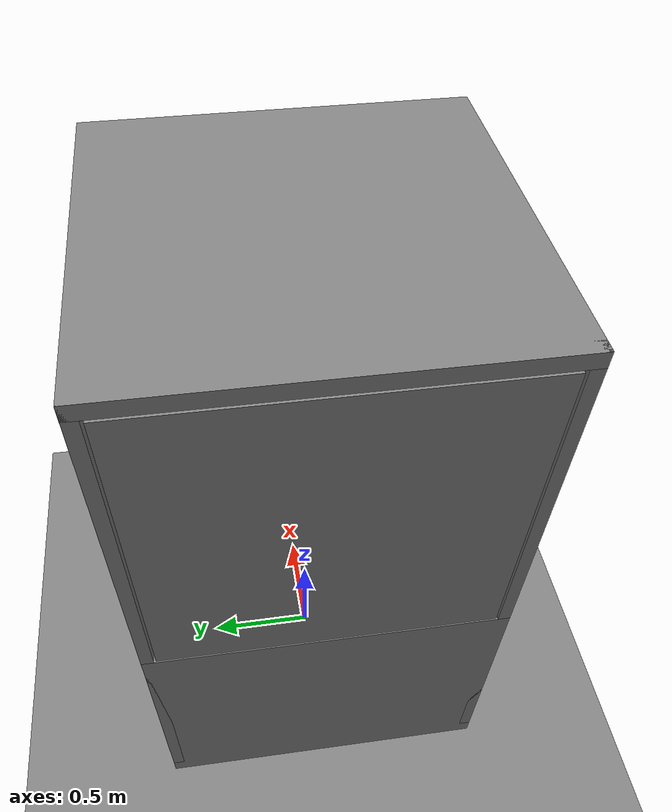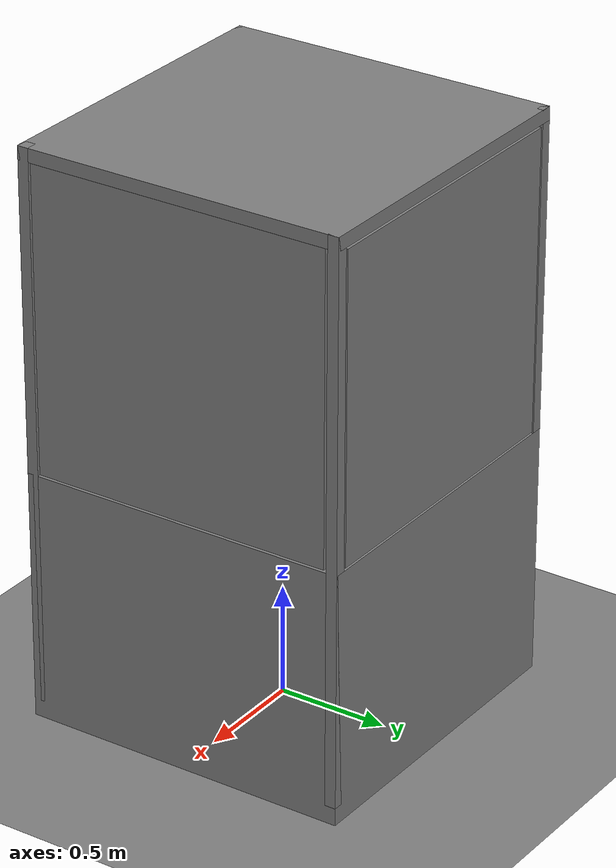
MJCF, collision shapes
<mujoco model="aic_world">
  <compiler angle="radian" />
  <option gravity="0 0 -9.8" magnetic="5.5645e-06 2.28758e-05 -4.23884e-05" />
  <visual>
    <headlight ambient="0.25 0.25 0.25" diffuse="0.5 0.5 0.5" specular="0.15 0.15 0.15" />
  </visual>
  <default>
    <default class="world_default" />
    <default class="cable_default">
      <joint damping="0.1" />
    </default>
  </default>
  <extension>
    <plugin plugin="mujoco.elasticity.cable">
      <instance name="composite">
        <config key="twist" value="1e2" />
        <config key="bend" value="4e1" />
      </instance>
    </plugin>
  </extension>
  <asset>
    <texture type="2d" colorspace="linear" name="texture_4d50ee79d050a658a0978573a6b2cfe5f0103f0e0858507c60cce7966154c700_floor_visual_Plane" file="4d50ee79d050a658a0978573a6b2cfe5f0103f0e0858507c60cce7966154c700_floor_visual_b3a94635-54d6beff6424435d3828cb4c8a1278d9ea3964b0.png" />
    <texture type="2d" colorspace="linear" name="texture_c4d55378de44a7d510e656ebd138527346b81da3a1c859716efb32a4b5adb56b_sc_port_visual_FOA-005A_3D_v1.006" file="c4d55378de44a7d510e656ebd138527346b81da3a1c859716efb32a4b5adb56b_sc_port_visual_dde5a3d8-80fba2240c77c79deed3a9c104fc19aae11de3a0.png" />
    <texture type="2d" colorspace="linear" name="texture_ef964132f42789e447f73cb7b6f7a63504cb1c7cc21c01bb1b3b76adb1890bd9_nic_card_visual_merged_0" file="ef964132f42789e447f73cb7b6f7a63504cb1c7cc21c01bb1b3b76adb1890bd9_nic_card_visual_45ced356-decb3c11fd49e8be2155fa2b1c64d354b4b1809a.png" />
    <texture type="2d" colorspace="linear" name="texture_ef964132f42789e447f73cb7b6f7a63504cb1c7cc21c01bb1b3b76adb1890bd9_nic_card_visual_merged_1" file="ef964132f42789e447f73cb7b6f7a63504cb1c7cc21c01bb1b3b76adb1890bd9_nic_card_visual_39dce63a-b1ab28e3f7e42255c5bb13a337e50008ebdbcb02.png" />
    <texture type="2d" colorspace="linear" name="texture_3c8f162873ab26f3c28d587135247b1ab9ef1a18a9d490deb9666be4c03443e6_sc_plug_visual_merged_0" file="3c8f162873ab26f3c28d587135247b1ab9ef1a18a9d490deb9666be4c03443e6_sc_plug_visual_5875f865-48f62b2f4840d852c7f39a01e6c183037dc1485b.png" />
    <texture type="2d" colorspace="linear" name="texture_b9fc682e4820b05cce436c98153fe0a21cf8357a9ca103d5872f530c3a9e2114_lc_plug_visual_merged_0" file="b9fc682e4820b05cce436c98153fe0a21cf8357a9ca103d5872f530c3a9e2114_lc_plug_visual_03dabf32-0905e8a8aa368516e682f6ec84258100cdb4efef.png" />
    <texture type="2d" colorspace="linear" name="texture_1c33e96b885803ba8f50d0e401fdc0b85ffce960d08fc167466b66b5712840ce_sfp_module_visual_Body.005" file="1c33e96b885803ba8f50d0e401fdc0b85ffce960d08fc167466b66b5712840ce_sfp_module_visual_8fc63b58-7471eafc55dcb668ae68adfe70a147b363ba3be9.png" />
    <texture type="2d" colorspace="linear" name="texture_1c33e96b885803ba8f50d0e401fdc0b85ffce960d08fc167466b66b5712840ce_sfp_module_visual_Body.005_1" file="1c33e96b885803ba8f50d0e401fdc0b85ffce960d08fc167466b66b5712840ce_sfp_module_visual_1f09e86a-a4dc4a72bd6e778067310898a5c179607fd78966.png" />
    <material name="material_9794a90dcadfa7aa02702c87bd7c3e051cdf9cc18ec0e90f598b09ed90d244f4_enclosure_visual_V1014952.001" class="world_default" shininess="0.5" rgba="0.2902 0.2902 0.2902 1.0000" specular="0.3" />
    <material name="material_9794a90dcadfa7aa02702c87bd7c3e051cdf9cc18ec0e90f598b09ed90d244f4_enclosure_visual_V1014952.001_1" class="world_default" shininess="0.5" rgba="0.2902 0.2902 0.2902 1.0000" specular="0.3" />
    <material name="material_9794a90dcadfa7aa02702c87bd7c3e051cdf9cc18ec0e90f598b09ed90d244f4_light_visual_Plane.001" class="world_default" shininess="10" rgba="1.0 0.98 0.95 0.9" emission="1.5" />
    <material name="material_4d50ee79d050a658a0978573a6b2cfe5f0103f0e0858507c60cce7966154c700_floor_visual_Plane" class="world_default" texture="texture_4d50ee79d050a658a0978573a6b2cfe5f0103f0e0858507c60cce7966154c700_floor_visual_Plane" shininess="30" rgba="0.5 0.5 0.5 1" />
    <material name="material_4d50ee79d050a658a0978573a6b2cfe5f0103f0e0858507c60cce7966154c700_walls_visual_Curve.001" class="world_default" shininess="0.9" rgba="0.85 0.9 0.95 0.25" specular="0.8" reflectance="0.3" />
    <material name="material_4d50ee79d050a658a0978573a6b2cfe5f0103f0e0858507c60cce7966154c700_walls_visual_merged_1" class="world_default" shininess="0.9" rgba="0.85 0.9 0.95 0.25" specular="0.8" reflectance="0.3" />
    <material name="material_4d50ee79d050a658a0978573a6b2cfe5f0103f0e0858507c60cce7966154c700_walls_visual_Plane.003_1" class="world_default" shininess="0.9" rgba="0.85 0.9 0.95 0.25" specular="0.8" reflectance="0.3" />
    <material name="material_4d50ee79d050a658a0978573a6b2cfe5f0103f0e0858507c60cce7966154c700_walls_visual_Plane.002" class="world_default" shininess="0.9" rgba="0.85 0.9 0.95 0.25" specular="0.8" reflectance="0.3" />
    <material name="material_bbecc21724e74143a9bbd9c42cd84dad13edf568a3b763c9e52bd1f3d93e96ac_base_visual_ISO_4762_-_M3_x_8.019" class="world_default" shininess="0.5" rgba="0.12 0.12 0.11 1.0" specular="0.3" />
    <material name="material_bbecc21724e74143a9bbd9c42cd84dad13edf568a3b763c9e52bd1f3d93e96ac_base_visual_ISO_4762_-_M3_x_8.019_1" class="world_default" shininess="0.5" rgba="0.0353 0.0353 0.0314 1.0000" specular="0.3" />
    <material name="material_bbecc21724e74143a9bbd9c42cd84dad13edf568a3b763c9e52bd1f3d93e96ac_base_visual_ISO_4762_-_M3_x_8.019_2" class="world_default" shininess="0.5" rgba="0.216 0.0 0.216 1.0" specular="0.3" />
    <material name="material_7ad515da736fc2c58c890d539f7e6b354f74c917d05e12c54574393bcc0acd27_sfp_mount_visual_ISO_4762_-_M2_x_8.011" class="world_default" shininess="0.5" rgba="0.18 0.18 0.18 1.0" specular="0.3" />
    <material name="material_7ad515da736fc2c58c890d539f7e6b354f74c917d05e12c54574393bcc0acd27_sfp_mount_visual_ISO_4762_-_M2_x_8.011_1" class="world_default" shininess="0.5" rgba="0.18 0.18 0.18 1.0" specular="0.3" />
    <material name="material_c4d55378de44a7d510e656ebd138527346b81da3a1c859716efb32a4b5adb56b_sc_port_visual_FOA-005A_3D_v1.006" class="world_default" texture="texture_c4d55378de44a7d510e656ebd138527346b81da3a1c859716efb32a4b5adb56b_sc_port_visual_FOA-005A_3D_v1.006" shininess="0.5" rgba="1.0 1.0 1.0 1.0" specular="0.3" />
    <material name="material_c4d55378de44a7d510e656ebd138527346b81da3a1c859716efb32a4b5adb56b_sc_port_visual_merged_1" class="world_default" shininess="0.5" rgba="0.15 0.3 0.7 1.0" specular="0.3" />
    <material name="material_c4d55378de44a7d510e656ebd138527346b81da3a1c859716efb32a4b5adb56b_sc_port_visual_merged_2" class="world_default" shininess="0.5" rgba="0.15 0.3 0.7 1.0" specular="0.3" />
    <material name="material_ef964132f42789e447f73cb7b6f7a63504cb1c7cc21c01bb1b3b76adb1890bd9_nic_card_mount_visual_ISO_4762_-_M2_x_8.054" class="world_default" shininess="0.5" rgba="0.2 0.2 0.18 1.0" specular="0.3" />
    <material name="material_ef964132f42789e447f73cb7b6f7a63504cb1c7cc21c01bb1b3b76adb1890bd9_nic_card_mount_visual_ISO_4762_-_M2_x_8.054_1" class="world_default" shininess="0.5" rgba="0.0353 0.0353 0.0314 1.0000" specular="0.3" />
    <material name="material_ef964132f42789e447f73cb7b6f7a63504cb1c7cc21c01bb1b3b76adb1890bd9_nic_card_visual_merged_0" class="world_default" texture="texture_ef964132f42789e447f73cb7b6f7a63504cb1c7cc21c01bb1b3b76adb1890bd9_nic_card_visual_merged_0" shininess="0.5" rgba="1.0 1.0 1.0 1.0" specular="0.3" />
    <material name="material_ef964132f42789e447f73cb7b6f7a63504cb1c7cc21c01bb1b3b76adb1890bd9_nic_card_visual_merged_1" class="world_default" texture="texture_ef964132f42789e447f73cb7b6f7a63504cb1c7cc21c01bb1b3b76adb1890bd9_nic_card_visual_merged_1" shininess="0.5" rgba="1.0 1.0 1.0 1.0" specular="0.3" />
    <material name="material_ef964132f42789e447f73cb7b6f7a63504cb1c7cc21c01bb1b3b76adb1890bd9_nic_card_visual_Plane.029" class="world_default" shininess="0.5" rgba="0.08 0.35 0.12 1.0" specular="0.3" />
    <material name="material_ef964132f42789e447f73cb7b6f7a63504cb1c7cc21c01bb1b3b76adb1890bd9_nic_card_visual_Cube.007" class="world_default" shininess="0.5" rgba="0.15 0.15 0.15 1.0" specular="0.3" />
    <material name="material_3c8f162873ab26f3c28d587135247b1ab9ef1a18a9d490deb9666be4c03443e6_sc_plug_visual_merged_0" class="world_default" texture="texture_3c8f162873ab26f3c28d587135247b1ab9ef1a18a9d490deb9666be4c03443e6_sc_plug_visual_merged_0" shininess="30" rgba="0.5 0.5 0.5 1" />
    <material name="material_b9fc682e4820b05cce436c98153fe0a21cf8357a9ca103d5872f530c3a9e2114_lc_plug_visual_merged_0" class="world_default" texture="texture_b9fc682e4820b05cce436c98153fe0a21cf8357a9ca103d5872f530c3a9e2114_lc_plug_visual_merged_0" shininess="30" rgba="0.5 0.5 0.5 1" />
    <material name="material_1c33e96b885803ba8f50d0e401fdc0b85ffce960d08fc167466b66b5712840ce_sfp_module_visual_Body.005" class="world_default" texture="texture_1c33e96b885803ba8f50d0e401fdc0b85ffce960d08fc167466b66b5712840ce_sfp_module_visual_Body.005" shininess="30" rgba="0.5 0.5 0.5 1" />
    <material name="material_1c33e96b885803ba8f50d0e401fdc0b85ffce960d08fc167466b66b5712840ce_sfp_module_visual_Body.005_1" class="world_default" texture="texture_1c33e96b885803ba8f50d0e401fdc0b85ffce960d08fc167466b66b5712840ce_sfp_module_visual_Body.005_1" shininess="30" rgba="0.5 0.5 0.5 1" />
    <mesh name="9794a90dcadfa7aa02702c87bd7c3e051cdf9cc18ec0e90f598b09ed90d244f4_enclosure_visual_V1014952.001" class="world_default" content_type="model/obj" file="9794a90dcadfa7aa02702c87bd7c3e051cdf9cc18ec0e90f598b09ed90d244f4_enclosure_visual_V1014952.001-c990efe7b9dfe87aa065fd6eb3960ce051ae2aef.obj" inertia="shell" />
    <mesh name="9794a90dcadfa7aa02702c87bd7c3e051cdf9cc18ec0e90f598b09ed90d244f4_enclosure_visual_V1014952.001_1" class="world_default" content_type="model/obj" file="9794a90dcadfa7aa02702c87bd7c3e051cdf9cc18ec0e90f598b09ed90d244f4_enclosure_visual_V1014952.001_1-807e07de06af157c84b994a232617507a7059420.obj" inertia="shell" />
    <mesh name="9794a90dcadfa7aa02702c87bd7c3e051cdf9cc18ec0e90f598b09ed90d244f4_light_visual_Plane.001" class="world_default" content_type="model/obj" file="9794a90dcadfa7aa02702c87bd7c3e051cdf9cc18ec0e90f598b09ed90d244f4_light_visual_Plane.001-a8a774a80bc239d73769a498eae528b206eebcb0.obj" inertia="shell" />
    <mesh name="4d50ee79d050a658a0978573a6b2cfe5f0103f0e0858507c60cce7966154c700_floor_visual_Plane" class="world_default" content_type="model/obj" file="4d50ee79d050a658a0978573a6b2cfe5f0103f0e0858507c60cce7966154c700_floor_visual_Plane-4dc7f6150ad7c239769a0860a01efb2015657aea.obj" inertia="shell" />
    <mesh name="4d50ee79d050a658a0978573a6b2cfe5f0103f0e0858507c60cce7966154c700_walls_visual_Curve.001" class="world_default" content_type="model/obj" file="4d50ee79d050a658a0978573a6b2cfe5f0103f0e0858507c60cce7966154c700_walls_visual_Curve.001-4d7c79ac2e958832fdb15589262141ca1b80d3a5.obj" inertia="shell" />
    <mesh name="4d50ee79d050a658a0978573a6b2cfe5f0103f0e0858507c60cce7966154c700_walls_visual_merged_1" class="world_default" content_type="model/obj" file="4d50ee79d050a658a0978573a6b2cfe5f0103f0e0858507c60cce7966154c700_walls_visual_merged_1-359a22140d528747936e80bedf90e1437a177a9f.obj" inertia="shell" />
    <mesh name="4d50ee79d050a658a0978573a6b2cfe5f0103f0e0858507c60cce7966154c700_walls_visual_Plane.003_1" class="world_default" content_type="model/obj" file="4d50ee79d050a658a0978573a6b2cfe5f0103f0e0858507c60cce7966154c700_walls_visual_Plane.003_1-cd05ed21fa19a2784fb772d7519abf7c31c8b85f.obj" inertia="shell" />
    <mesh name="4d50ee79d050a658a0978573a6b2cfe5f0103f0e0858507c60cce7966154c700_walls_visual_Plane.002" class="world_default" content_type="model/obj" file="4d50ee79d050a658a0978573a6b2cfe5f0103f0e0858507c60cce7966154c700_walls_visual_Plane.002-ee4f781765eec46c2256d941981732d4b1857f24.obj" inertia="shell" />
    <mesh name="bbecc21724e74143a9bbd9c42cd84dad13edf568a3b763c9e52bd1f3d93e96ac_base_visual_ISO_4762_-_M3_x_8.019" class="world_default" content_type="model/obj" file="bbecc21724e74143a9bbd9c42cd84dad13edf568a3b763c9e52bd1f3d93e96ac_base_visual_ISO_4762_-_M3_x_8.019-f814bb518c42769543ab6246809f3fe4af5c2b64.obj" inertia="shell" />
    <mesh name="bbecc21724e74143a9bbd9c42cd84dad13edf568a3b763c9e52bd1f3d93e96ac_base_visual_ISO_4762_-_M3_x_8.019_1" class="world_default" content_type="model/obj" file="bbecc21724e74143a9bbd9c42cd84dad13edf568a3b763c9e52bd1f3d93e96ac_base_visual_ISO_4762_-_M3_x_8.019_1-0b276ba9910a7642121235b62d2afc47c3995782.obj" inertia="shell" />
    <mesh name="bbecc21724e74143a9bbd9c42cd84dad13edf568a3b763c9e52bd1f3d93e96ac_base_visual_ISO_4762_-_M3_x_8.019_2" class="world_default" content_type="model/obj" file="bbecc21724e74143a9bbd9c42cd84dad13edf568a3b763c9e52bd1f3d93e96ac_base_visual_ISO_4762_-_M3_x_8.019_2-7b96569be9572803417c5650ee83c9c883b44191.obj" inertia="shell" />
    <mesh name="7ad515da736fc2c58c890d539f7e6b354f74c917d05e12c54574393bcc0acd27_sfp_mount_visual_ISO_4762_-_M2_x_8.011" class="world_default" content_type="model/obj" file="7ad515da736fc2c58c890d539f7e6b354f74c917d05e12c54574393bcc0acd27_sfp_mount_visual_ISO_4762_-_M2_x_8.011-e79a298280ce559f60558a5df64e118c814f63e4.obj" inertia="shell" />
    <mesh name="7ad515da736fc2c58c890d539f7e6b354f74c917d05e12c54574393bcc0acd27_sfp_mount_visual_ISO_4762_-_M2_x_8.011_1" class="world_default" content_type="model/obj" file="7ad515da736fc2c58c890d539f7e6b354f74c917d05e12c54574393bcc0acd27_sfp_mount_visual_ISO_4762_-_M2_x_8.011_1-3a79ef8883f6645921d3fa2c67cf381141e6ea26.obj" inertia="shell" />
    <mesh name="c4d55378de44a7d510e656ebd138527346b81da3a1c859716efb32a4b5adb56b_sc_port_visual_FOA-005A_3D_v1.006" class="world_default" content_type="model/obj" file="c4d55378de44a7d510e656ebd138527346b81da3a1c859716efb32a4b5adb56b_sc_port_visual_FOA-005A_3D_v1.006-0690c54f8a7d5fd325c57bdd49f081ad4db184ec.obj" inertia="shell" />
    <mesh name="c4d55378de44a7d510e656ebd138527346b81da3a1c859716efb32a4b5adb56b_sc_port_visual_merged_1" class="world_default" content_type="model/obj" file="c4d55378de44a7d510e656ebd138527346b81da3a1c859716efb32a4b5adb56b_sc_port_visual_merged_1-31aef5141da75eeb5a734da46bb7eaf48a169650.obj" inertia="shell" />
    <mesh name="c4d55378de44a7d510e656ebd138527346b81da3a1c859716efb32a4b5adb56b_sc_port_visual_merged_2" class="world_default" content_type="model/obj" file="c4d55378de44a7d510e656ebd138527346b81da3a1c859716efb32a4b5adb56b_sc_port_visual_merged_2-a5eaa459350ec83eadeb09501472b99f6092b833.obj" inertia="shell" />
    <mesh name="ef964132f42789e447f73cb7b6f7a63504cb1c7cc21c01bb1b3b76adb1890bd9_nic_card_mount_visual_ISO_4762_-_M2_x_8.054" class="world_default" content_type="model/obj" file="ef964132f42789e447f73cb7b6f7a63504cb1c7cc21c01bb1b3b76adb1890bd9_nic_card_mount_visual_ISO_4762_-_M2_x_8.054-865f98896565b646973302f5cc3bb20e1474682a.obj" inertia="shell" />
    <mesh name="ef964132f42789e447f73cb7b6f7a63504cb1c7cc21c01bb1b3b76adb1890bd9_nic_card_mount_visual_ISO_4762_-_M2_x_8.054_1" class="world_default" content_type="model/obj" file="ef964132f42789e447f73cb7b6f7a63504cb1c7cc21c01bb1b3b76adb1890bd9_nic_card_mount_visual_ISO_4762_-_M2_x_8.054_1-5adcf23490bd5794ededbd17ac1064f40ca2f1d8.obj" inertia="shell" />
    <mesh name="ef964132f42789e447f73cb7b6f7a63504cb1c7cc21c01bb1b3b76adb1890bd9_nic_card_visual_merged_0" class="world_default" content_type="model/obj" file="ef964132f42789e447f73cb7b6f7a63504cb1c7cc21c01bb1b3b76adb1890bd9_nic_card_visual_merged_0-b45f6200bfaa68e87732b114c99af8b477e66413.obj" inertia="shell" />
    <mesh name="ef964132f42789e447f73cb7b6f7a63504cb1c7cc21c01bb1b3b76adb1890bd9_nic_card_visual_merged_1" class="world_default" content_type="model/obj" file="ef964132f42789e447f73cb7b6f7a63504cb1c7cc21c01bb1b3b76adb1890bd9_nic_card_visual_merged_1-0e349b7b61b9f4e172feb5320f1e8146f966f938.obj" inertia="shell" />
    <mesh name="ef964132f42789e447f73cb7b6f7a63504cb1c7cc21c01bb1b3b76adb1890bd9_nic_card_visual_Plane.029" class="world_default" content_type="model/obj" file="ef964132f42789e447f73cb7b6f7a63504cb1c7cc21c01bb1b3b76adb1890bd9_nic_card_visual_Plane.029-3e628f059a97b4e803370a2b5e0abfcfac063972.obj" inertia="shell" />
    <mesh name="ef964132f42789e447f73cb7b6f7a63504cb1c7cc21c01bb1b3b76adb1890bd9_nic_card_visual_Cube.007" class="world_default" content_type="model/obj" file="ef964132f42789e447f73cb7b6f7a63504cb1c7cc21c01bb1b3b76adb1890bd9_nic_card_visual_Cube.007-f8fbe4a2582482ceb99cb3e87bdf6d5a3daf05ec.obj" inertia="shell" />
    <mesh name="3c8f162873ab26f3c28d587135247b1ab9ef1a18a9d490deb9666be4c03443e6_sc_plug_visual_merged_0" class="world_default" content_type="model/obj" file="3c8f162873ab26f3c28d587135247b1ab9ef1a18a9d490deb9666be4c03443e6_sc_plug_visual_merged_0-67f94accf247f722dd4954d7448d7956402901f2.obj" inertia="shell" />
    <mesh name="b9fc682e4820b05cce436c98153fe0a21cf8357a9ca103d5872f530c3a9e2114_lc_plug_visual_merged_0" class="world_default" content_type="model/obj" file="b9fc682e4820b05cce436c98153fe0a21cf8357a9ca103d5872f530c3a9e2114_lc_plug_visual_merged_0-fdaf59710fc3cc118a7df05add4ff4205edda4ef.obj" inertia="shell" />
    <mesh name="1c33e96b885803ba8f50d0e401fdc0b85ffce960d08fc167466b66b5712840ce_sfp_module_visual_Body.005" class="world_default" content_type="model/obj" file="1c33e96b885803ba8f50d0e401fdc0b85ffce960d08fc167466b66b5712840ce_sfp_module_visual_Body.005-f93147e1e403de321fb70c06a4b1e00f20feb9fd.obj" inertia="shell" />
    <mesh name="1c33e96b885803ba8f50d0e401fdc0b85ffce960d08fc167466b66b5712840ce_sfp_module_visual_Body.005_1" class="world_default" content_type="model/obj" file="1c33e96b885803ba8f50d0e401fdc0b85ffce960d08fc167466b66b5712840ce_sfp_module_visual_Body.005_1-4af964a95522e2593eb6381eca4f09ef239782c7.obj" inertia="shell" />
    <material name="glass_wall" rgba="0.85 0.9 0.95 0.12" specular="0.8" shininess="0.9" reflectance="0.3" />
    <material name="light_panel_ceiling" rgba="1.0 0.98 0.95 0.8" emission="1.0" specular="0.05" />
    <material name="debug_red" rgba="1 0 0 1" specular="0.5" shininess="0.5" />
    <mesh name="manual_nic_card" file="manual_nic_card.obj" scale="1 1 1" />
    <mesh name="manual_sc_port" file="manual_sc_port.obj" scale="0.001 0.001 0.001" />
    <mesh name="manual_lc_mount" file="manual_lc_mount.obj" />
    <mesh name="manual_sc_mount" file="manual_sc_mount.obj" />
    <material name="nic_green" rgba="0.1 0.5 0.15 1" specular="0.3" />
    <material name="sc_blue" rgba="0.15 0.25 0.7 1" specular="0.4" />
    <material name="mount_grey" rgba="0.35 0.35 0.35 1" specular="0.3" />
    <material name="plug_blue" rgba="0.15 0.4 0.85 1" specular="0.4" />
  </asset>
  <worldbody>
    <light name="enclosure_light" class="world_default" pos="0 0 2.5" dir="0 0 -1" intensity="0.4" range="2" attenuation="1 0.01 0.001" cutoff="114.592" exponent="0.993023" diffuse="1 1 1" specular="0.1 0.1 0.1" />
    <light name="ceiling_01" class="world_default" pos="2 2 6" dir="0 0 -1" intensity="2" range="9" castshadow="false" attenuation="1 0.01 0.001" cutoff="360" diffuse="1 1 1" specular="0.1 0.1 0.1" />
    <light name="ceiling_02" class="world_default" pos="-2 -2 6" dir="0 0 -1" intensity="2" range="9" castshadow="false" attenuation="1 0.01 0.001" cutoff="360" diffuse="1 1 1" specular="0.1 0.1 0.1" />
    <body name="enclosure_link">
      <inertial pos="0 0 0" mass="1" diaginertia="1 1 1" />
      <geom name="v1015026001_collider_box" class="world_default" size="0.75 0.569492 0.75" pos="-0.010998 0.009283 0.569706" quat="1.22475e-07 -1.22474e-07 0.707107 0.707107" type="box" group="3" />
      <geom name="v1015028001_collider_box" class="world_default" size="0.0254 0.0254 1.25" pos="0.713602 0.733883 1.3292" quat="1.73205e-07 0 0 -1" type="box" group="3" />
      <geom name="v1015013001_collider_box" class="world_default" size="0.0304 0.75 0.75" pos="-0.010998 0.009283 2.5488" quat="0.707107 0 -0.707107 0" type="box" group="3" />
      <geom name="v1015027_collider_box" class="world_default" size="0.0254 0.0254 1.25" pos="-0.735598 0.733883 1.3292" quat="1.73205e-07 0 0 -1" type="box" group="3" />
      <geom name="v1015029_collider_box" class="world_default" size="0.0254 0.0254 1.25" pos="-0.735598 -0.715317 1.3292" quat="0 1.73205e-07 -1 -1.73205e-07" type="box" group="3" />
      <geom name="v1015030_collider_box" class="world_default" size="0.0254 0.0254 1.25" pos="0.713602 -0.715317 1.3292" quat="1.73205e-07 0 0 -1" type="box" group="3" />
      <geom name="enclosure_visual" class="world_default" type="mesh" contype="0" conaffinity="0" material="material_9794a90dcadfa7aa02702c87bd7c3e051cdf9cc18ec0e90f598b09ed90d244f4_enclosure_visual_V1014952.001" mesh="9794a90dcadfa7aa02702c87bd7c3e051cdf9cc18ec0e90f598b09ed90d244f4_enclosure_visual_V1014952.001" />
      <geom name="enclosure_visual_0" class="world_default" type="mesh" contype="0" conaffinity="0" material="material_9794a90dcadfa7aa02702c87bd7c3e051cdf9cc18ec0e90f598b09ed90d244f4_enclosure_visual_V1014952.001_1" mesh="9794a90dcadfa7aa02702c87bd7c3e051cdf9cc18ec0e90f598b09ed90d244f4_enclosure_visual_V1014952.001_1" />
      <geom name="light_visual" class="world_default" type="mesh" contype="0" conaffinity="0" material="material_9794a90dcadfa7aa02702c87bd7c3e051cdf9cc18ec0e90f598b09ed90d244f4_light_visual_Plane.001" mesh="9794a90dcadfa7aa02702c87bd7c3e051cdf9cc18ec0e90f598b09ed90d244f4_light_visual_Plane.001" />
    </body>
    <body name="enclosure_walls_link">
      <inertial pos="0 0 0" mass="1" diaginertia="1 1 1" />
      <geom name="v1015062006_collider_box" class="world_default" size="0.0250005 0.6796 0.6892" pos="-0.010998 0.734284 1.8288" quat="0.5 0.5 -0.5 -0.5" type="box" group="3" />
      <geom name="v1015062005_collider_box" class="world_default" size="0.6892 0.6796 0.025" pos="-0.735998 0.009283 1.8288" quat="0.5 0.5 -0.5 -0.5" type="box" group="3" />
      <geom name="v1015062007_collider_box" class="world_default" size="0.025 0.6846 0.6892" pos="-0.010998 -0.715717 1.8338" quat="0.5 0.5 -0.5 -0.5" type="box" group="3" />
      <geom name="v1015062008_collider_box" class="world_default" size="0.6892 0.6846 0.025" pos="0.714002 0.009283 1.8338" quat="0.5 0.5 -0.5 -0.5" type="box" group="3" />
    </body>
    <body name="floor_link">
      <inertial pos="0 0 0" mass="1" diaginertia="1 1 1" />
      <geom name="floor_cylinder" class="world_default" size="5 5 1" type="plane" group="3" />
      <geom name="floor_visual" class="world_default" type="mesh" contype="0" conaffinity="0" material="material_4d50ee79d050a658a0978573a6b2cfe5f0103f0e0858507c60cce7966154c700_floor_visual_Plane" mesh="4d50ee79d050a658a0978573a6b2cfe5f0103f0e0858507c60cce7966154c700_floor_visual_Plane" />
      <geom name="walls_visual" class="world_default" type="mesh" contype="0" conaffinity="0" material="material_4d50ee79d050a658a0978573a6b2cfe5f0103f0e0858507c60cce7966154c700_walls_visual_Curve.001" mesh="4d50ee79d050a658a0978573a6b2cfe5f0103f0e0858507c60cce7966154c700_walls_visual_Curve.001" />
      <geom name="walls_visual_0" class="world_default" type="mesh" contype="0" conaffinity="0" material="material_4d50ee79d050a658a0978573a6b2cfe5f0103f0e0858507c60cce7966154c700_walls_visual_merged_1" mesh="4d50ee79d050a658a0978573a6b2cfe5f0103f0e0858507c60cce7966154c700_walls_visual_merged_1" />
      <geom name="walls_visual_1" class="world_default" type="mesh" contype="0" conaffinity="0" material="material_4d50ee79d050a658a0978573a6b2cfe5f0103f0e0858507c60cce7966154c700_walls_visual_Plane.003_1" mesh="4d50ee79d050a658a0978573a6b2cfe5f0103f0e0858507c60cce7966154c700_walls_visual_Plane.003_1" />
      <geom name="walls_visual_2" class="world_default" type="mesh" contype="0" conaffinity="0" material="material_4d50ee79d050a658a0978573a6b2cfe5f0103f0e0858507c60cce7966154c700_walls_visual_Plane.002" mesh="4d50ee79d050a658a0978573a6b2cfe5f0103f0e0858507c60cce7966154c700_walls_visual_Plane.002" />
    </body>
    <body name="task_board_base_link" pos="0.15 -0.2 1.14" quat="4.63111e-05 -1.74943e-08 3.66001e-09 1">
      <inertial pos="0.00107843 -0.00208333 0.000196078" quat="0.715076 0.657801 0.160161 0.174107" mass="5.1" diaginertia="0.102413 0.102413 0.101" />
      <geom name="task_board_base_link_fixed_joint_lump__v1015083001_collider_box_left_collision" class="world_default" size="0.15 0.114 0.0045" pos="0 -0.1 0.0075" type="box" group="3" />
      <geom name="task_board_base_link_fixed_joint_lump__v1015083001_collider_right_collision_1" class="world_default" size="0.15 0.0635 0.0045" pos="0 0.149 0.0075" type="box" group="3" />
      <geom name="task_board_base_link_fixed_joint_lump__v1015083001_collider_mid_collision_2" class="world_default" size="0.07 0.006 0.0045" pos="-0.075 0.05 0.0075" type="box" group="3" />
      <geom name="task_board_base_link_fixed_joint_lump__v1015083001_collider_bottom_collision_3" class="world_default" size="0.0825 0.2125 0.0045" pos="0.068 0 0.0075" type="box" group="3" />
      <geom name="task_board_base_link_fixed_joint_lump__v1015083001_collider_top_collision_4" class="world_default" size="0.0075 0.2125 0.0045" pos="-0.143 0 0.0075" type="box" group="3" />
      <geom name="task_board_base_link_fixed_joint_lump__iso_4762_m2_x_8072_collider_box_collision_5" class="world_default" size="0.0147285 0.008875 0.0025" pos="0.088272 -0.10625 0.0125" type="box" group="3" />
      <geom name="task_board_base_link_fixed_joint_lump__iso_4762_m2_x_8072_collider_box_001_collision_6" class="world_default" size="0.0192665 0.008875 0.000864" pos="0.071366 -0.10625 0.027144" quat="0.92388 0 -0.382683 0" type="box" group="3" />
      <geom name="task_board_base_link_fixed_joint_lump__iso_4762_m2_x_8072_collider_box_002_collision_7" class="world_default" size="0.0137425 0.008875 0.001844" pos="0.083636 -0.10625 0.022684" quat="0.92388 0 -0.382683 0" type="box" group="3" />
      <geom name="task_board_base_link_fixed_joint_lump__iso_4762_m2_x_8072_collider_box_003_collision_8" class="world_default" size="0.0180555 0.0011525 0.005478" pos="0.076242 -0.098527 0.023979" quat="0.92388 0 -0.382683 0" type="box" group="3" />
      <geom name="task_board_base_link_fixed_joint_lump__iso_4762_m2_x_8072_collider_box_004_collision_9" class="world_default" size="0.0180555 0.0009375 0.005815" pos="0.076003 -0.114188 0.024217" quat="0.92388 0 -0.382683 0" type="box" group="3" />
      <geom name="task_board_base_link_fixed_joint_lump__iso_4762_m2_x_8072_collider_box_005_collision_10" class="world_default" size="0.002532 0.008875 0.005815" pos="0.065017 -0.10625 0.013231" quat="0.92388 0 -0.382683 0" type="box" group="3" />
      <geom name="task_board_base_link_fixed_joint_lump__iso_4762_m2_x_8072_collider_box_006_collision_11" class="world_default" size="0.0071855 0.008875 0.0025" pos="0.0592 -0.10625 0.0125" type="box" group="3" />
      <geom name="task_board_base_link_fixed_joint_lump__iso_4762_m2_x_8072_collider_box_007_collision_12" class="world_default" size="0.0024465 0.008875 0.0083775" pos="0.091553 -0.10625 0.021771" type="box" group="3" />
      <geom name="task_board_base_link_fixed_joint_lump__base_visual_visual" class="world_default" type="mesh" contype="0" conaffinity="0" material="material_bbecc21724e74143a9bbd9c42cd84dad13edf568a3b763c9e52bd1f3d93e96ac_base_visual_ISO_4762_-_M3_x_8.019" mesh="bbecc21724e74143a9bbd9c42cd84dad13edf568a3b763c9e52bd1f3d93e96ac_base_visual_ISO_4762_-_M3_x_8.019" />
      <geom name="task_board_base_link_fixed_joint_lump__base_visual_visual_0" class="world_default" type="mesh" contype="0" conaffinity="0" material="material_bbecc21724e74143a9bbd9c42cd84dad13edf568a3b763c9e52bd1f3d93e96ac_base_visual_ISO_4762_-_M3_x_8.019_1" mesh="bbecc21724e74143a9bbd9c42cd84dad13edf568a3b763c9e52bd1f3d93e96ac_base_visual_ISO_4762_-_M3_x_8.019_1" />
      <geom name="task_board_base_link_fixed_joint_lump__base_visual_visual_1" class="world_default" type="mesh" contype="0" conaffinity="0" material="material_bbecc21724e74143a9bbd9c42cd84dad13edf568a3b763c9e52bd1f3d93e96ac_base_visual_ISO_4762_-_M3_x_8.019_2" mesh="bbecc21724e74143a9bbd9c42cd84dad13edf568a3b763c9e52bd1f3d93e96ac_base_visual_ISO_4762_-_M3_x_8.019_2" />
      <geom name="task_board_base_link_fixed_joint_lump__sfp_mount_visual_visual_1" class="world_default" pos="0.055 -0.10625 0.01" quat="1 0 0 0" type="mesh" contype="0" conaffinity="0" material="material_7ad515da736fc2c58c890d539f7e6b354f74c917d05e12c54574393bcc0acd27_sfp_mount_visual_ISO_4762_-_M2_x_8.011" mesh="7ad515da736fc2c58c890d539f7e6b354f74c917d05e12c54574393bcc0acd27_sfp_mount_visual_ISO_4762_-_M2_x_8.011" />
      <geom name="task_board_base_link_fixed_joint_lump__sfp_mount_visual_visual_1_0" class="world_default" pos="0.055 -0.10625 0.01" quat="1 0 0 0" type="mesh" contype="0" conaffinity="0" material="material_7ad515da736fc2c58c890d539f7e6b354f74c917d05e12c54574393bcc0acd27_sfp_mount_visual_ISO_4762_-_M2_x_8.011_1" mesh="7ad515da736fc2c58c890d539f7e6b354f74c917d05e12c54574393bcc0acd27_sfp_mount_visual_ISO_4762_-_M2_x_8.011_1" />
      <body name="sc_port_0::sc_port_link" pos="-0.090947 0.029500 0.016500" quat="0.500398 0.5 0.499602 0.5">
        <inertial pos="0 -0.00100271 0.000137321" quat="-0.00185702 0.707104 -0.00185702 0.707104" mass="0.04" diaginertia="6.5519e-06 5.50329e-06 1.86262e-06" />
        <geom name="cube_collider_box" class="world_default" size="0.0008435 0.013716 0.00465" pos="0.012047 0 0" type="box" group="3" />
        <geom name="cube_collider_box.001" class="world_default" size="0.0128905 0.0054 0.000425" pos="0 0 0.004225" type="box" group="3" />
        <geom name="cube_collider_box_mid" class="world_default" size="0.00515 0.013716 0.0003" pos="0 0 0.00435" type="box" group="3" />
        <geom name="cube_collider_box_mid02" class="world_default" size="0.0025 0.013716 0.0003" pos="0.01 0 0.00435" type="box" group="3" />
        <geom name="cube_collider_box_mid03" class="world_default" size="0.0025 0.013716 0.0003" pos="-0.01 0 0.00435" type="box" group="3" />
        <geom name="cube_collider_box.002" class="world_default" size="0.012825 0.013716 0.0003" pos="0 0 -0.00435" type="box" group="3" />
        <geom name="cube_collider_box.003" class="world_default" size="0.0008435 0.013716 0.00465" pos="-0.012047 0 0" type="box" group="3" />
        <geom name="cube_collider_box.004" class="world_default" size="0.002742 0.001524 0.00465" pos="-0.014683 0 0" type="box" group="3" />
        <geom name="cube_collider_box.005" class="world_default" size="0.002742 0.001524 0.00465" pos="0.014683 0 0" type="box" group="3" />
        <geom name="cube_collider_box.006" class="world_default" size="0.001496 0.013716 0.00465" type="box" group="3" />
        <geom name="v1015120013_collider_box" class="world_default" size="0.006 0.005 0.0015" pos="0.0183 -0.003 0" quat="0.5 -0.5 0.5 0.5" type="box" group="3" />
        <geom name="v1015120012_collider_box" class="world_default" size="0.006 0.005 0.0015" pos="-0.0183 -0.003 0" quat="0.5 -0.5 -0.5 -0.5" type="box" group="3" />
        <geom name="iso 4762 - m2 x 6013_collider_cylinder" class="world_default" size="0.0019 0.004" pos="0.0153 -0.0005 0" quat="0.693475 0.693475 0.138174 -0.138174" type="cylinder" group="3" />
        <geom name="iso 4762 - m2 x 6012_collider_cylinder" class="world_default" size="0.0019 0.004" pos="-0.0153 -0.0005 0" quat="0.693475 0.693475 0.138174 -0.138174" type="cylinder" group="3" />
        <geom name="contact_collision" class="world_default" size="0.0125 0.001473 0.0045" pos="0 -0.0034 0" quat="1.73205e-07 -1 0 0" type="box" group="3" />
        <geom name="sc_port_visual" class="world_default" type="mesh" contype="0" conaffinity="0" material="material_c4d55378de44a7d510e656ebd138527346b81da3a1c859716efb32a4b5adb56b_sc_port_visual_FOA-005A_3D_v1.006" mesh="c4d55378de44a7d510e656ebd138527346b81da3a1c859716efb32a4b5adb56b_sc_port_visual_FOA-005A_3D_v1.006" />
        <geom name="sc_port_visual_0" class="world_default" type="mesh" contype="0" conaffinity="0" material="material_c4d55378de44a7d510e656ebd138527346b81da3a1c859716efb32a4b5adb56b_sc_port_visual_merged_1" mesh="c4d55378de44a7d510e656ebd138527346b81da3a1c859716efb32a4b5adb56b_sc_port_visual_merged_1" />
        <geom name="sc_port_visual_1" class="world_default" type="mesh" contype="0" conaffinity="0" material="material_c4d55378de44a7d510e656ebd138527346b81da3a1c859716efb32a4b5adb56b_sc_port_visual_merged_2" mesh="c4d55378de44a7d510e656ebd138527346b81da3a1c859716efb32a4b5adb56b_sc_port_visual_merged_2" />
        <site name="sc_port_sensor" class="world_default" pos="0 0 0" />
        <body name="sc_port_base_link" pos="0 -0.002 0" quat="-9.38184e-07 -9.38187e-07 -0.707105 0.707108">
          <inertial pos="0 0 0" mass="1" diaginertia="1 1 1" />
          <body name="sc_port_base_link_entrance" pos="0 0 -0.01564">
            <inertial pos="0 0 0" mass="1" diaginertia="1 1 1" />
          </body>
        </body>
      </body>
      <body name="nic_card_mount_0::nic_card_mount_link" pos="-0.091763 -0.174500 0.012000">
        <inertial pos="0 0 0" mass="1" diaginertia="1 1 1" />
        <geom name="v1015085006_collider_box" class="world_default" size="0.0025035 0.036998 0.0775" pos="0.006002 -0.025497 0.0875" quat="0.707107 0 0 0.707107" type="box" group="3" />
        <geom name="v1015085006_collider_box.001" class="world_default" size="0.0125 0.01075 0.007" pos="-0.0555 -0.0155 0.172" quat="0.707107 0 0 0.707107" type="box" group="3" />
        <geom name="v1015085006_collider_box.002" class="world_default" size="0.01375 0.002532 0.0515" pos="0.038535 -0.01425 0.1155" quat="0.707107 0 0 0.707107" type="box" group="3" />
        <geom name="v1015085006_collider_box.003" class="world_default" size="0.010003 0.044894 0.0075" pos="-0.001997 -0.017997 0.0075" quat="0.707107 0 0 0.707107" type="box" group="3" />
        <geom name="v1015085006_collider_box004_collider_box" class="world_default" size="0.0025005 0.02575 0.0075" pos="-0.042132 -0.025499 0.151803" quat="0.653335 0.270468 0.270468 0.653335" type="box" group="3" />
        <geom name="v1015085006_collider_box.005" class="world_default" size="0.008 0.01 0.0075" pos="-0.043 -0.0198 0.1665" quat="0.65401 0.268834 0.268834 0.654009" type="box" group="3" />
        <geom name="v1015085011_collider_box" class="world_default" size="0.0078345 0.031 0.0025" pos="3e-06 -0.004871 0.0025" quat="0.707107 0 0 0.707107" type="box" group="3" />
        <geom name="nic_card_mount_visual" class="world_default" type="mesh" contype="0" conaffinity="0" material="material_ef964132f42789e447f73cb7b6f7a63504cb1c7cc21c01bb1b3b76adb1890bd9_nic_card_mount_visual_ISO_4762_-_M2_x_8.054" mesh="ef964132f42789e447f73cb7b6f7a63504cb1c7cc21c01bb1b3b76adb1890bd9_nic_card_mount_visual_ISO_4762_-_M2_x_8.054" />
        <geom name="nic_card_mount_visual_0" class="world_default" type="mesh" contype="0" conaffinity="0" material="material_ef964132f42789e447f73cb7b6f7a63504cb1c7cc21c01bb1b3b76adb1890bd9_nic_card_mount_visual_ISO_4762_-_M2_x_8.054_1" mesh="ef964132f42789e447f73cb7b6f7a63504cb1c7cc21c01bb1b3b76adb1890bd9_nic_card_mount_visual_ISO_4762_-_M2_x_8.054_1" />
        <body name="nic_card_link" pos="-0.002 -0.01785 0.0899" quat="0.707388 -0.706825 0 0">
          <inertial pos="0.00150732 -0.00850988 0.00340281" quat="0.506895 0.50066 -0.499024 0.493328" mass="0.15" diaginertia="0.000228137 0.000185186 4.94971e-05" />
          <geom name="pcb_collider_box" class="world_default" size="0.028 0.0725 0.0008" pos="0 0 -0.0008" type="box" group="3" />
          <geom name="pcb_collider_box.001" class="world_default" size="0.0345 0.0255 0.0008" pos="0.0065 -0.0025 -0.0008" type="box" group="3" />
          <geom name="pcb_collider_box.002" class="world_default" size="0.032 0.04775 0.0008" pos="0.004 -0.02475 -0.0008" type="box" group="3" />
          <geom name="cylinder015_collider_cylinder" class="world_default" size="0.00268 0.002757" pos="0.03175 -0.063 -0.000988" type="cylinder" group="3" />
          <geom name="cylinder017_collider_cylinder" class="world_default" size="0.00268 0.002759" pos="-0.02225 -0.0675 -0.000986" type="cylinder" group="3" />
          <geom name="pcb001_collider_box" class="world_default" size="0.005125 0.005125 0.0023015" pos="0.015105 0.054161 0.001899" type="box" group="3" />
          <geom name="pcb024_collider_box" class="world_default" size="0.0034 0.0034 0.002162" pos="-0.015586 0.055516 0.001759" type="box" group="3" />
          <geom name="pcb033_collider_box" class="world_default" size="0.021537 0.0208075 0.0011515" pos="-0.002297 0.046302 0.000749" type="box" group="3" />
          <geom name="cube001_collider_box" class="world_default" size="0.002 0.07 0.00575" pos="0.025006 -0.00041 0.00575" type="box" group="3" />
          <geom name="cube001_collider_box.001" class="world_default" size="0.0235 0.026 0.0055" pos="-0.0029 -0.0015 0.008" type="box" group="3" />
          <geom name="10099100-011lfc001_collider_box" class="world_default" size="0.0005495 0.02436 0.0055415" pos="-0.018049 -0.052954 0.00548" quat="0.00675028 0.999977 0 0" type="box" group="3" />
          <geom name="10099100-011lfc001_collider_box.001" class="world_default" size="0.0005625 0.02436 0.0055605" pos="-0.002437 -0.052954 0.005461" quat="0.00675028 0.999977 0 0" type="box" group="3" />
          <geom name="10099100-011lfc001_collider_box.002" class="world_default" size="0.008112 0.02436 0.0004615" pos="-0.010237 -0.052889 0.010484" quat="0.00675028 0.999977 0 0" type="box" group="3" />
          <geom name="10099100-011lfc001_collider_box.003" class="world_default" size="0.008112 0.02436 0.000527" pos="-0.010237 -0.053024 4.6e-05" quat="0.00675028 0.999977 0 0" type="box" group="3" />
          <geom name="10099100-011lfc001_collider_box.004" class="world_default" size="0.008112 0.000125 0.006849" pos="-0.010237 -0.028738 0.003845" quat="0.00675028 0.999977 0 0" type="box" group="3" />
          <geom name="10099100-011lfc001_collider_box.005" class="world_default" size="0.0005495 0.02436 0.0055415" pos="0.005151 -0.052954 0.00548" quat="0.00675028 0.999977 0 0" type="box" group="3" />
          <geom name="10099100-011lfc001_collider_box.006" class="world_default" size="0.0005625 0.02436 0.0055605" pos="0.020763 -0.052954 0.005461" quat="0.00675028 0.999977 0 0" type="box" group="3" />
          <geom name="10099100-011lfc001_collider_box.007" class="world_default" size="0.008112 0.02436 0.0004615" pos="0.012963 -0.052889 0.010484" quat="0.00675028 0.999977 0 0" type="box" group="3" />
          <geom name="10099100-011lfc001_collider_box.008" class="world_default" size="0.008112 0.02436 0.000527" pos="0.012963 -0.053024 4.6e-05" quat="0.00675028 0.999977 0 0" type="box" group="3" />
          <geom name="10099100-011lfc001_collider_box.009" class="world_default" size="0.008112 0.000125 0.006849" pos="0.012963 -0.028738 0.003845" quat="0.00675028 0.999977 0 0" type="box" group="3" />
          <geom name="plane001_collider_box" class="world_default" size="0.056701 0.0004375 0.0017245" pos="-0.007649 -0.074646 -0.000751" type="box" group="3" />
          <geom name="plane001_collider_box.001" class="world_default" size="0.056701 0.0004375 0.002505" pos="-0.007649 -0.074646 0.01352" type="box" group="3" />
          <geom name="plane001_collider_box.002" class="world_default" size="0.0180905 0.0004375 0.0055615" pos="0.038559 -0.074646 0.006455" type="box" group="3" />
          <geom name="plane001_collider_box.003" class="world_default" size="0.023089 0.0004375 0.0055615" pos="-0.041261 -0.074646 0.006455" type="box" group="3" />
          <geom name="plane001_collider_box.004" class="world_default" size="0.0004375 0.00635 0.0105" pos="-0.063913 -0.080558 0.005525" type="box" group="3" />
          <geom name="plane001_collider_box.005" class="world_default" size="0.032 0.007498 0.0012375" pos="0.004 -0.067206 -0.001238" type="box" group="3" />
          <geom name="cube001_collider_box.002" class="world_default" size="0.0215 0.024 0.0015745" pos="-0.0029 -0.0015 0.001228" type="box" group="3" />
          <geom name="plane001_collider_box.006" class="world_default" size="0.038092 0.001584 0.0004385" pos="-0.005942 -0.073499 0.015586" type="box" group="3" />
          <geom name="contact_collision_01" class="world_default" size="0.004056 0.000125 0.00125" pos="0.012963 -0.0305 0.002845" quat="0.00675028 0.999977 0 0" type="box" group="3" />
          <geom name="contact_collision_02" class="world_default" size="0.004056 0.000125 0.00125" pos="-0.010237 -0.0305 0.002845" quat="0.00675028 0.999977 0 0" type="box" group="3" />
          <geom name="contact_collision_01_holder" class="world_default" size="0.004056 0.000125 0.001" pos="0.012963 -0.03 0.008" quat="0.00675028 0.999977 0 0" type="box" group="3" />
          <geom name="contact_collision_02_holder" class="world_default" size="0.004056 0.000125 0.001" pos="-0.010237 -0.03 0.008" quat="0.00675028 0.999977 0 0" type="box" group="3" />
          <geom name="nic_card_visual" class="world_default" type="mesh" contype="0" conaffinity="0" material="material_ef964132f42789e447f73cb7b6f7a63504cb1c7cc21c01bb1b3b76adb1890bd9_nic_card_visual_merged_0" mesh="ef964132f42789e447f73cb7b6f7a63504cb1c7cc21c01bb1b3b76adb1890bd9_nic_card_visual_merged_0" />
          <geom name="nic_card_visual_0" class="world_default" type="mesh" contype="0" conaffinity="0" material="material_ef964132f42789e447f73cb7b6f7a63504cb1c7cc21c01bb1b3b76adb1890bd9_nic_card_visual_merged_1" mesh="ef964132f42789e447f73cb7b6f7a63504cb1c7cc21c01bb1b3b76adb1890bd9_nic_card_visual_merged_1" />
          <geom name="nic_card_visual_1" class="world_default" type="mesh" contype="0" conaffinity="0" material="material_ef964132f42789e447f73cb7b6f7a63504cb1c7cc21c01bb1b3b76adb1890bd9_nic_card_visual_Plane.029" mesh="ef964132f42789e447f73cb7b6f7a63504cb1c7cc21c01bb1b3b76adb1890bd9_nic_card_visual_Plane.029" />
          <geom name="nic_card_visual_2" class="world_default" type="mesh" contype="0" conaffinity="0" material="material_ef964132f42789e447f73cb7b6f7a63504cb1c7cc21c01bb1b3b76adb1890bd9_nic_card_visual_Cube.007" mesh="ef964132f42789e447f73cb7b6f7a63504cb1c7cc21c01bb1b3b76adb1890bd9_nic_card_visual_Cube.007" />
          <site name="sfp_port_sensor" class="world_default" pos="0 0 0" />
          <body name="sfp_port_0_link" pos="0.01295 -0.031572 0.00501" quat="0.702339 -0.711842 0 0">
            <inertial pos="0 0 0" mass="1" diaginertia="1 1 1" />
            <body name="sfp_port_0_link_entrance" pos="0 0 -0.0458">
              <inertial pos="0 0 0" mass="1" diaginertia="1 1 1" />
            </body>
          </body>
          <body name="sfp_port_1_link" pos="-0.01025 -0.031572 0.00501" quat="0.702339 -0.711842 0 0">
            <inertial pos="0 0 0" mass="1" diaginertia="1 1 1" />
            <body name="sfp_port_1_link_entrance" pos="0 0 -0.0458">
              <inertial pos="0 0 0" mass="1" diaginertia="1 1 1" />
            </body>
          </body>
        </body>
      </body>
      <body name="nic_card_mount_3::nic_card_mount_link_r3" pos="-0.068800 -0.054500 0.012000">
        <inertial pos="0 0 0" mass="1" diaginertia="1 1 1" />
        <geom name="nic_card_mount_visual_r3" class="world_default" type="mesh" contype="0" conaffinity="0" material="material_ef964132f42789e447f73cb7b6f7a63504cb1c7cc21c01bb1b3b76adb1890bd9_nic_card_mount_visual_ISO_4762_-_M2_x_8.054" mesh="ef964132f42789e447f73cb7b6f7a63504cb1c7cc21c01bb1b3b76adb1890bd9_nic_card_mount_visual_ISO_4762_-_M2_x_8.054" />
        <geom name="nic_card_mount_visual_0_r3" class="world_default" type="mesh" contype="0" conaffinity="0" material="material_ef964132f42789e447f73cb7b6f7a63504cb1c7cc21c01bb1b3b76adb1890bd9_nic_card_mount_visual_ISO_4762_-_M2_x_8.054_1" mesh="ef964132f42789e447f73cb7b6f7a63504cb1c7cc21c01bb1b3b76adb1890bd9_nic_card_mount_visual_ISO_4762_-_M2_x_8.054_1" />
        <body name="nic_card_link_3" pos="-0.002 -0.01785 0.0899" quat="0.707388 -0.706825 0 0">
          <inertial pos="0.00150732 -0.00850988 0.00340281" quat="0.506895 0.50066 -0.499024 0.493328" mass="0.15" diaginertia="0.000228137 0.000185186 4.94971e-05" />
          <geom name="nic_card_visual_r3" class="world_default" type="mesh" contype="0" conaffinity="0" material="material_ef964132f42789e447f73cb7b6f7a63504cb1c7cc21c01bb1b3b76adb1890bd9_nic_card_visual_merged_0" mesh="ef964132f42789e447f73cb7b6f7a63504cb1c7cc21c01bb1b3b76adb1890bd9_nic_card_visual_merged_0" />
          <geom name="nic_card_visual_0_r3" class="world_default" type="mesh" contype="0" conaffinity="0" material="material_ef964132f42789e447f73cb7b6f7a63504cb1c7cc21c01bb1b3b76adb1890bd9_nic_card_visual_merged_1" mesh="ef964132f42789e447f73cb7b6f7a63504cb1c7cc21c01bb1b3b76adb1890bd9_nic_card_visual_merged_1" />
          <geom name="nic_card_visual_1_r3" class="world_default" type="mesh" contype="0" conaffinity="0" material="material_ef964132f42789e447f73cb7b6f7a63504cb1c7cc21c01bb1b3b76adb1890bd9_nic_card_visual_Plane.029" mesh="ef964132f42789e447f73cb7b6f7a63504cb1c7cc21c01bb1b3b76adb1890bd9_nic_card_visual_Plane.029" />
          <geom name="nic_card_visual_2_r3" class="world_default" type="mesh" contype="0" conaffinity="0" material="material_ef964132f42789e447f73cb7b6f7a63504cb1c7cc21c01bb1b3b76adb1890bd9_nic_card_visual_Cube.007" mesh="ef964132f42789e447f73cb7b6f7a63504cb1c7cc21c01bb1b3b76adb1890bd9_nic_card_visual_Cube.007" />
          <site name="sfp_port_sensor_r3" class="world_default" pos="0 0 0" />
          <body name="sfp_port_0_link_r3" pos="0.01295 -0.031572 0.00501" quat="0.702339 -0.711842 0 0">
            <inertial pos="0 0 0" mass="1" diaginertia="1 1 1" />
            <body name="sfp_port_0_link_entrance_r3" pos="0 0 -0.0458">
              <inertial pos="0 0 0" mass="1" diaginertia="1 1 1" />
            </body>
          </body>
          <body name="sfp_port_1_link_r3" pos="-0.01025 -0.031572 0.00501" quat="0.702339 -0.711842 0 0">
            <inertial pos="0 0 0" mass="1" diaginertia="1 1 1" />
            <body name="sfp_port_1_link_entrance_r3" pos="0 0 -0.0458">
              <inertial pos="0 0 0" mass="1" diaginertia="1 1 1" />
            </body>
          </body>
        </body>
      </body>
      <body name="nic_card_mount_4::nic_card_mount_link_r4" pos="-0.091641 -0.014500 0.012000">
        <inertial pos="0 0 0" mass="1" diaginertia="1 1 1" />
        <geom name="nic_card_mount_visual_r4" class="world_default" type="mesh" contype="0" conaffinity="0" material="material_ef964132f42789e447f73cb7b6f7a63504cb1c7cc21c01bb1b3b76adb1890bd9_nic_card_mount_visual_ISO_4762_-_M2_x_8.054" mesh="ef964132f42789e447f73cb7b6f7a63504cb1c7cc21c01bb1b3b76adb1890bd9_nic_card_mount_visual_ISO_4762_-_M2_x_8.054" />
        <geom name="nic_card_mount_visual_0_r4" class="world_default" type="mesh" contype="0" conaffinity="0" material="material_ef964132f42789e447f73cb7b6f7a63504cb1c7cc21c01bb1b3b76adb1890bd9_nic_card_mount_visual_ISO_4762_-_M2_x_8.054_1" mesh="ef964132f42789e447f73cb7b6f7a63504cb1c7cc21c01bb1b3b76adb1890bd9_nic_card_mount_visual_ISO_4762_-_M2_x_8.054_1" />
        <body name="nic_card_link_4" pos="-0.002 -0.01785 0.0899" quat="0.707388 -0.706825 0 0">
          <inertial pos="0.00150732 -0.00850988 0.00340281" quat="0.506895 0.50066 -0.499024 0.493328" mass="0.15" diaginertia="0.000228137 0.000185186 4.94971e-05" />
          <geom name="nic_card_visual_r4" class="world_default" type="mesh" contype="0" conaffinity="0" material="material_ef964132f42789e447f73cb7b6f7a63504cb1c7cc21c01bb1b3b76adb1890bd9_nic_card_visual_merged_0" mesh="ef964132f42789e447f73cb7b6f7a63504cb1c7cc21c01bb1b3b76adb1890bd9_nic_card_visual_merged_0" />
          <geom name="nic_card_visual_0_r4" class="world_default" type="mesh" contype="0" conaffinity="0" material="material_ef964132f42789e447f73cb7b6f7a63504cb1c7cc21c01bb1b3b76adb1890bd9_nic_card_visual_merged_1" mesh="ef964132f42789e447f73cb7b6f7a63504cb1c7cc21c01bb1b3b76adb1890bd9_nic_card_visual_merged_1" />
          <geom name="nic_card_visual_1_r4" class="world_default" type="mesh" contype="0" conaffinity="0" material="material_ef964132f42789e447f73cb7b6f7a63504cb1c7cc21c01bb1b3b76adb1890bd9_nic_card_visual_Plane.029" mesh="ef964132f42789e447f73cb7b6f7a63504cb1c7cc21c01bb1b3b76adb1890bd9_nic_card_visual_Plane.029" />
          <geom name="nic_card_visual_2_r4" class="world_default" type="mesh" contype="0" conaffinity="0" material="material_ef964132f42789e447f73cb7b6f7a63504cb1c7cc21c01bb1b3b76adb1890bd9_nic_card_visual_Cube.007" mesh="ef964132f42789e447f73cb7b6f7a63504cb1c7cc21c01bb1b3b76adb1890bd9_nic_card_visual_Cube.007" />
          <site name="sfp_port_sensor_r4" class="world_default" pos="0 0 0" />
          <body name="sfp_port_0_link_r4" pos="0.01295 -0.031572 0.00501" quat="0.702339 -0.711842 0 0">
            <inertial pos="0 0 0" mass="1" diaginertia="1 1 1" />
            <body name="sfp_port_0_link_entrance_r4" pos="0 0 -0.0458">
              <inertial pos="0 0 0" mass="1" diaginertia="1 1 1" />
            </body>
          </body>
          <body name="sfp_port_1_link_r4" pos="-0.01025 -0.031572 0.00501" quat="0.702339 -0.711842 0 0">
            <inertial pos="0 0 0" mass="1" diaginertia="1 1 1" />
            <body name="sfp_port_1_link_entrance_r4" pos="0 0 -0.0458">
              <inertial pos="0 0 0" mass="1" diaginertia="1 1 1" />
            </body>
          </body>
        </body>
      </body>
      <body name="sc_port_1::sc_port_link_sc1" pos="-0.056305 0.070500 0.016500" quat="0.500398 0.5 0.499602 0.5">
        <inertial pos="0 -0.00100271 0.000137321" quat="-0.00185702 0.707104 -0.00185702 0.707104" mass="0.04" diaginertia="6.5519e-06 5.50329e-06 1.86262e-06" />
        <geom name="sc_port_visual_sc1" class="world_default" type="mesh" contype="0" conaffinity="0" material="material_c4d55378de44a7d510e656ebd138527346b81da3a1c859716efb32a4b5adb56b_sc_port_visual_FOA-005A_3D_v1.006" mesh="c4d55378de44a7d510e656ebd138527346b81da3a1c859716efb32a4b5adb56b_sc_port_visual_FOA-005A_3D_v1.006" />
        <geom name="sc_port_visual_0_sc1" class="world_default" type="mesh" contype="0" conaffinity="0" material="material_c4d55378de44a7d510e656ebd138527346b81da3a1c859716efb32a4b5adb56b_sc_port_visual_merged_1" mesh="c4d55378de44a7d510e656ebd138527346b81da3a1c859716efb32a4b5adb56b_sc_port_visual_merged_1" />
        <geom name="sc_port_visual_1_sc1" class="world_default" type="mesh" contype="0" conaffinity="0" material="material_c4d55378de44a7d510e656ebd138527346b81da3a1c859716efb32a4b5adb56b_sc_port_visual_merged_2" mesh="c4d55378de44a7d510e656ebd138527346b81da3a1c859716efb32a4b5adb56b_sc_port_visual_merged_2" />
        <site name="sc_port_sensor_sc1" class="world_default" pos="0 0 0" />
        <body name="sc_port_base_link_sc1" pos="0 -0.002 0" quat="-9.38184e-07 -9.38187e-07 -0.707105 0.707108">
          <inertial pos="0 0 0" mass="1" diaginertia="1 1 1" />
          <body name="sc_port_base_link_entrance_sc1" pos="0 0 -0.01564">
            <inertial pos="0 0 0" mass="1" diaginertia="1 1 1" />
          </body>
        </body>
      </body>
      <body name="sfp_mount_0_body" pos="0.055000 0.049600 0.012000">
        <inertial pos="0 0 0" mass="0.05" diaginertia="1e-5 1e-5 1e-5" />
        <geom name="sfp_mount_0_visual_0" type="mesh" mesh="7ad515da736fc2c58c890d539f7e6b354f74c917d05e12c54574393bcc0acd27_sfp_mount_visual_ISO_4762_-_M2_x_8.011" material="material_7ad515da736fc2c58c890d539f7e6b354f74c917d05e12c54574393bcc0acd27_sfp_mount_visual_ISO_4762_-_M2_x_8.011" contype="0" conaffinity="0" />
        <geom name="sfp_mount_0_visual_1" type="mesh" mesh="7ad515da736fc2c58c890d539f7e6b354f74c917d05e12c54574393bcc0acd27_sfp_mount_visual_ISO_4762_-_M2_x_8.011_1" material="material_7ad515da736fc2c58c890d539f7e6b354f74c917d05e12c54574393bcc0acd27_sfp_mount_visual_ISO_4762_-_M2_x_8.011_1" contype="0" conaffinity="0" />
        <geom name="sfp_mod_in_mount_0_0" type="mesh" mesh="1c33e96b885803ba8f50d0e401fdc0b85ffce960d08fc167466b66b5712840ce_sfp_module_visual_Body.005" material="material_1c33e96b885803ba8f50d0e401fdc0b85ffce960d08fc167466b66b5712840ce_sfp_module_visual_Body.005" contype="0" conaffinity="0" />
        <geom name="sfp_mod_in_mount_0_1" type="mesh" mesh="1c33e96b885803ba8f50d0e401fdc0b85ffce960d08fc167466b66b5712840ce_sfp_module_visual_Body.005_1" material="material_1c33e96b885803ba8f50d0e401fdc0b85ffce960d08fc167466b66b5712840ce_sfp_module_visual_Body.005_1" contype="0" conaffinity="0" />
      </body>
      <body name="lc_mount_1_body" pos="0.010000 0.167008 0.012000">
        <inertial pos="0 0 0" mass="0.05" diaginertia="1e-5 1e-5 1e-5" />
        <geom name="lc_mount_1_visual_0" type="mesh" mesh="manual_lc_mount" material="mount_grey" contype="0" conaffinity="0" />
        <geom name="lc_plug_in_mount_1_0" type="mesh" mesh="b9fc682e4820b05cce436c98153fe0a21cf8357a9ca103d5872f530c3a9e2114_lc_plug_visual_merged_0" material="material_b9fc682e4820b05cce436c98153fe0a21cf8357a9ca103d5872f530c3a9e2114_lc_plug_visual_merged_0" contype="0" conaffinity="0" />
      </body>
      <body name="sc_mount_2_body" pos="0.100000 -0.113510 0.012000">
        <inertial pos="0 0 0" mass="0.05" diaginertia="1e-5 1e-5 1e-5" />
        <geom name="sc_mount_2_visual_0" type="mesh" mesh="manual_sc_mount" material="mount_grey" contype="0" conaffinity="0" />
        <geom name="sc_plug_in_mount_2_0" type="mesh" mesh="3c8f162873ab26f3c28d587135247b1ab9ef1a18a9d490deb9666be4c03443e6_sc_plug_visual_merged_0" material="material_3c8f162873ab26f3c28d587135247b1ab9ef1a18a9d490deb9666be4c03443e6_sc_plug_visual_merged_0" contype="0" conaffinity="0" />
      </body>
    </body>
    <body name="cable_end_0" childclass="cable_default" pos="0.171400 0.020606 1.511889" quat="0.712741 0.312130 -0.052173 0.625982">
      <freejoint name="cable_end_0_free" />
      <inertial pos="0 0 0" mass="0.0025" diaginertia="1e-6 1e-6 1e-6" />
      <geom name="base_vis" class="world_default" size="0.002" contype="0" conaffinity="0" />
      <plugin instance="composite" />
      <body name="cable_connection_0" pos="-3.40043e-08 1.67663e-08 -1.41876e-07" quat="0.92541 -0.0906116 -0.328563 0.165687">
        <inertial pos="0 0 0" mass="0.01" diaginertia="1e-6 1e-6 1e-6" />
        <joint name="joint_connection_end_0" class="world_default" pos="0 0 0" type="ball" damping="0.2" />
        <geom name="visual_0_0" class="world_default" size="0.001 0.00180278" pos="-0.00180278 0.002 0" quat="0.676768 0.204909 0.676764 -0.204908" type="cylinder" contype="0" conaffinity="0" />
        <geom name="visual_1_0" class="world_default" size="0.001 0.00180278" pos="-0.00180278 -0.002 0" quat="0.676768 -0.204909 0.676764 0.204908" type="cylinder" contype="0" conaffinity="0" />
        <plugin instance="composite" />
        <body name="link_1" pos="0.00202509 -0.00566879 -0.0232329" quat="-0.0725775 -0.263018 -0.956472 0.103517">
          <inertial pos="0 0 0" mass="0.0025" diaginertia="1e-6 1e-6 1e-6" />
          <joint name="joint_end_0" pos="0 0 -0.024" type="ball" />
          <geom name="link_1_collision" size="0.002 0.018" pos="0 0 0.006" type="cylinder" group="3" />
          <geom name="sphere_1_collision" size="0.002" pos="0 0 0.024" group="3" />
          <geom name="link_1_vis" size="0.002 0.024" type="cylinder" contype="0" conaffinity="0" />
          <geom name="sphere_1_vis" size="0.002" pos="0 0 0.024" contype="0" conaffinity="0" />
          <plugin instance="composite" />
          <body name="link_2" pos="0.00584501 -0.00752224 0.0460289" quat="0.978998 0.157177 0.127936 -0.0221662">
            <inertial pos="0 0 0" mass="0.0025" diaginertia="1e-6 1e-6 1e-6" />
            <joint name="joint_1" pos="0 0 -0.024" type="ball" />
            <geom name="link_2_collision" size="0.002 0.024" type="cylinder" group="3" />
            <geom name="sphere_2_collision" size="0.002" pos="0 0 0.024" group="3" />
            <geom name="link_2_vis" size="0.002 0.024" type="cylinder" contype="0" conaffinity="0" />
            <geom name="sphere_2_vis" size="0.002" pos="0 0 0.024" contype="0" conaffinity="0" />
            <plugin instance="composite" />
            <body name="link_3" pos="0.000233021 -0.00664298 0.0470614" quat="0.989939 0.139627 0.00792586 -0.0214838">
              <inertial pos="0 0 0" mass="0.0025" diaginertia="1e-6 1e-6 1e-6" />
              <joint name="joint_2" pos="0 0 -0.024" type="ball" />
              <geom name="link_3_collision" size="0.002 0.024" type="cylinder" group="3" />
              <geom name="sphere_3_collision" size="0.002" pos="0 0 0.024" group="3" />
              <geom name="link_3_vis" size="0.002 0.024" type="cylinder" contype="0" conaffinity="0" />
              <geom name="sphere_3_vis" size="0.002" pos="0 0 0.024" contype="0" conaffinity="0" />
              <plugin instance="composite" />
              <body name="link_4" pos="-0.00226399 -0.00466992 0.0474323" quat="0.99376 0.0990215 -0.0450057 -0.0246991">
                <inertial pos="0 0 0" mass="0.0025" diaginertia="1e-6 1e-6 1e-6" />
                <joint name="joint_3" pos="0 0 -0.024" type="ball" />
                <geom name="link_4_collision" size="0.002 0.024" type="cylinder" group="3" />
                <geom name="sphere_4_collision" size="0.002" pos="0 0 0.024" group="3" />
                <geom name="link_4_vis" size="0.002 0.024" type="cylinder" contype="0" conaffinity="0" />
                <geom name="sphere_4_vis" size="0.002" pos="0 0 0.024" contype="0" conaffinity="0" />
                <plugin instance="composite" />
                <body name="link_5" pos="-0.00370357 -0.00314857 0.0475031" quat="0.993983 0.0690352 -0.0748138 -0.0404312">
                  <inertial pos="0 0 0" mass="0.0025" diaginertia="1e-6 1e-6 1e-6" />
                  <joint name="joint_4" pos="0 0 -0.024" type="ball" />
                  <geom name="link_5_collision" size="0.002 0.024" type="cylinder" group="3" />
                  <geom name="sphere_5_collision" size="0.002" pos="0 0 0.024" group="3" />
                  <geom name="link_5_vis" size="0.002 0.024" type="cylinder" contype="0" conaffinity="0" />
                  <geom name="sphere_5_vis" size="0.002" pos="0 0 0.024" contype="0" conaffinity="0" />
                  <plugin instance="composite" />
                  <body name="link_6" pos="-0.0040031 -0.00179911 0.0475956" quat="0.993728 0.0429358 -0.0811867 -0.0638018">
                    <inertial pos="0 0 0" mass="0.0025" diaginertia="1e-6 1e-6 1e-6" />
                    <joint name="joint_5" pos="0 0 -0.024" type="ball" />
                    <geom name="link_6_collision" size="0.002 0.024" type="cylinder" group="3" />
                    <geom name="sphere_6_collision" size="0.002" pos="0 0 0.024" group="3" />
                    <geom name="link_6_vis" size="0.002 0.024" type="cylinder" contype="0" conaffinity="0" />
                    <geom name="sphere_6_vis" size="0.002" pos="0 0 0.024" contype="0" conaffinity="0" />
                    <plugin instance="composite" />
                    <body name="link_7" pos="-0.00350972 -0.000708282 0.0477319" quat="0.993366 0.0211582 -0.0717488 -0.0873414">
                      <inertial pos="0 0 0" mass="0.0025" diaginertia="1e-6 1e-6 1e-6" />
                      <joint name="joint_6" pos="0 0 -0.024" type="ball" />
                      <geom name="link_7_collision" size="0.002 0.024" type="cylinder" group="3" />
                      <geom name="sphere_7_collision" size="0.002" pos="0 0 0.024" group="3" />
                      <geom name="link_7_vis" size="0.002 0.024" type="cylinder" contype="0" conaffinity="0" />
                      <geom name="sphere_7_vis" size="0.002" pos="0 0 0.024" contype="0" conaffinity="0" />
                      <plugin instance="composite" />
                      <body name="link_8" pos="-0.00240982 0.000201041 0.0478786" quat="0.993431 0.0009921 -0.0504393 -0.102715">
                        <inertial pos="0 0 0" mass="0.0025" diaginertia="1e-6 1e-6 1e-6" />
                        <joint name="joint_7" pos="0 0 -0.024" type="ball" />
                        <geom name="link_8_collision" size="0.002 0.024" type="cylinder" group="3" />
                        <geom name="sphere_8_collision" size="0.002" pos="0 0 0.024" group="3" />
                        <geom name="link_8_vis" size="0.002 0.024" type="cylinder" contype="0" conaffinity="0" />
                        <geom name="sphere_8_vis" size="0.002" pos="0 0 0.024" contype="0" conaffinity="0" />
                        <plugin instance="composite" />
                        <body name="link_9" pos="-0.00116902 0.00100383 0.0479516" quat="0.993969 -0.0182547 -0.0264257 -0.104856">
                          <inertial pos="0 0 0" mass="0.0025" diaginertia="1e-6 1e-6 1e-6" />
                          <joint name="joint_8" pos="0 0 -0.024" type="ball" />
                          <geom name="link_9_collision" size="0.002 0.024" type="cylinder" group="3" />
                          <geom name="sphere_9_collision" size="0.002" pos="0 0 0.024" group="3" />
                          <geom name="link_9_vis" size="0.002 0.024" type="cylinder" contype="0" conaffinity="0" />
                          <geom name="sphere_9_vis" size="0.002" pos="0 0 0.024" contype="0" conaffinity="0" />
                          <plugin instance="composite" />
                          <body name="link_10" pos="-0.000281793 0.00176528 0.0479338" quat="0.994695 -0.0360499 -0.0093865 -0.0958885">
                            <inertial pos="0 0 0" mass="0.0025" diaginertia="1e-6 1e-6 1e-6" />
                            <joint name="joint_9" pos="0 0 -0.024" type="ball" />
                            <geom name="link_10_collision" size="0.002 0.024" type="cylinder" group="3" />
                            <geom name="sphere_10_collision" size="0.002" pos="0 0 0.024" group="3" />
                            <geom name="link_10_vis" size="0.002 0.024" type="cylinder" contype="0" conaffinity="0" />
                            <geom name="sphere_10_vis" size="0.002" pos="0 0 0.024" contype="0" conaffinity="0" />
                            <plugin instance="composite" />
                            <body name="link_11" pos="0.00127222 0.00268138 0.0478168" quat="0.993831 -0.0581807 0.0212724 -0.0919961">
                              <inertial pos="0 0 0" mass="0.0025" diaginertia="1e-6 1e-6 1e-6" />
                              <joint name="joint_10" pos="0 0 -0.024" type="ball" />
                              <geom name="link_11_collision" size="0.002 0.024" type="cylinder" group="3" />
                              <geom name="sphere_11_collision" size="0.002" pos="0 0 0.024" group="3" />
                              <geom name="link_11_vis" size="0.002 0.024" type="cylinder" contype="0" conaffinity="0" />
                              <geom name="sphere_11_vis" size="0.002" pos="0 0 0.024" contype="0" conaffinity="0" />
                              <plugin instance="composite" />
                              <body name="link_12" pos="0.00326444 0.00422176 0.0474009" quat="0.991342 -0.0930306 0.0621487 -0.0687278">
                                <inertial pos="0 0 0" mass="0.0025" diaginertia="1e-6 1e-6 1e-6" />
                                <joint name="joint_11" pos="0 0 -0.024" type="ball" />
                                <geom name="link_12_collision" size="0.002 0.024" type="cylinder" group="3" />
                                <geom name="sphere_12_collision" size="0.002" pos="0 0 0.024" group="3" />
                                <geom name="link_12_vis" size="0.002 0.024" type="cylinder" contype="0" conaffinity="0" />
                                <geom name="sphere_12_vis" size="0.002" pos="0 0 0.024" contype="0" conaffinity="0" />
                                <plugin instance="composite" />
                                <body name="link_13" pos="0.00481492 0.00598385 0.0467386" quat="0.985876 -0.130533 0.0961796 -0.0419319">
                                  <inertial pos="0 0 0" mass="0.0025" diaginertia="1e-6 1e-6 1e-6" />
                                  <joint name="joint_12" pos="0 0 -0.024" type="ball" />
                                  <geom name="link_13_collision" size="0.002 0.024" type="cylinder" group="3" />
                                  <geom name="sphere_13_collision" size="0.002" pos="0 0 0.024" group="3" />
                                  <geom name="link_13_vis" size="0.002 0.024" type="cylinder" contype="0" conaffinity="0" />
                                  <geom name="sphere_13_vis" size="0.002" pos="0 0 0.024" contype="0" conaffinity="0" />
                                  <plugin instance="composite" />
                                  <body name="link_14" pos="0.00590745 0.00750702 0.0460178" quat="0.979002 -0.161713 0.123125 -0.0156329">
                                    <inertial pos="0 0 0" mass="0.0025" diaginertia="1e-6 1e-6 1e-6" />
                                    <joint name="joint_13" pos="0 0 -0.024" type="ball" />
                                    <geom name="link_14_collision" size="0.002 0.024" type="cylinder" group="3" />
                                    <geom name="sphere_14_collision" size="0.002" pos="0 0 0.024" group="3" />
                                    <geom name="link_14_vis" size="0.002 0.024" type="cylinder" contype="0" conaffinity="0" />
                                    <geom name="sphere_14_vis" size="0.002" pos="0 0 0.024" contype="0" conaffinity="0" />
                                    <plugin instance="composite" />
                                    <body name="link_15" pos="0.00664116 0.00818823 0.045561" quat="0.974228 -0.173923 0.143413 0.00793697">
                                      <inertial pos="0 0 0" mass="0.0025" diaginertia="1e-6 1e-6 1e-6" />
                                      <joint name="joint_14" pos="0 0 -0.024" type="ball" />
                                      <geom name="link_15_collision" size="0.002 0.024" type="cylinder" group="3" />
                                      <geom name="sphere_15_collision" size="0.002" pos="0 0 0.024" group="3" />
                                      <geom name="link_15_vis" size="0.002 0.024" type="cylinder" contype="0" conaffinity="0" />
                                      <geom name="sphere_15_vis" size="0.002" pos="0 0 0.024" contype="0" conaffinity="0" />
                                      <plugin instance="composite" />
                                      <body name="link_16" pos="0.00692449 0.00768018 0.0456596" quat="0.974934 -0.159966 0.152334 0.0266436">
                                        <inertial pos="0 0 0" mass="0.0025" diaginertia="1e-6 1e-6 1e-6" />
                                        <joint name="joint_15" pos="0 0 -0.024" type="ball" />
                                        <geom name="link_16_collision" size="0.002 0.024" type="cylinder" group="3" />
                                        <geom name="sphere_16_collision" size="0.002" pos="0 0 0.024" group="3" />
                                        <geom name="link_16_vis" size="0.002 0.024" type="cylinder" contype="0" conaffinity="0" />
                                        <geom name="sphere_16_vis" size="0.002" pos="0 0 0.024" contype="0" conaffinity="0" />
                                        <plugin instance="composite" />
                                        <body name="link_17" pos="0.00681819 0.00605233 0.0462025" quat="0.980315 -0.122659 0.149746 0.0388934">
                                          <inertial pos="0 0 0" mass="0.0025" diaginertia="1e-6 1e-6 1e-6" />
                                          <joint name="joint_16" pos="0 0 -0.024" type="ball" />
                                          <geom name="link_17_collision" size="0.002 0.024" type="cylinder" group="3" />
                                          <geom name="sphere_17_collision" size="0.002" pos="0 0 0.024" group="3" />
                                          <geom name="link_17_vis" size="0.002 0.024" type="cylinder" contype="0" conaffinity="0" />
                                          <geom name="sphere_17_vis" size="0.002" pos="0 0 0.024" contype="0" conaffinity="0" />
                                          <plugin instance="composite" />
                                          <body name="link_18" pos="0.00641735 0.00357584 0.0468482" quat="0.986986 -0.0694066 0.138496 0.0431305">
                                            <inertial pos="0 0 0" mass="0.0025" diaginertia="1e-6 1e-6 1e-6" />
                                            <joint name="joint_17" pos="0 0 -0.024" type="ball" />
                                            <geom name="link_18_collision" size="0.002 0.024" type="cylinder" group="3" />
                                            <geom name="sphere_18_collision" size="0.002" pos="0 0 0.024" group="3" />
                                            <geom name="link_18_vis" size="0.002 0.024" type="cylinder" contype="0" conaffinity="0" />
                                            <geom name="sphere_18_vis" size="0.002" pos="0 0 0.024" contype="0" conaffinity="0" />
                                            <plugin instance="composite" />
                                            <body name="link_19" pos="0.00637488 0.0013839 0.0470975" quat="0.989822 -0.0239852 0.135093 0.037785">
                                              <inertial pos="0 0 0" mass="0.0025" diaginertia="1e-6 1e-6 1e-6" />
                                              <joint name="joint_18" pos="0 0 -0.024" type="ball" />
                                              <geom name="link_19_collision" size="0.002 0.024" type="cylinder" group="3" />
                                              <geom name="sphere_19_collision" size="0.002" pos="0 0 0.024" group="3" />
                                              <geom name="link_19_vis" size="0.002 0.024" type="cylinder" contype="0" conaffinity="0" />
                                              <geom name="sphere_19_vis" size="0.002" pos="0 0 0.024" contype="0" conaffinity="0" />
                                              <plugin instance="composite" />
                                              <body name="link_20" pos="0.00586409 -0.00106164 0.0472503" quat="0.991756 0.0257196 0.122456 0.027624">
                                                <inertial pos="0 0 0" mass="0.0025" diaginertia="1e-6 1e-6 1e-6" />
                                                <joint name="joint_19" pos="0 0 -0.024" type="ball" />
                                                <geom name="link_20_collision" size="0.002 0.024" type="cylinder" group="3" />
                                                <geom name="sphere_20_collision" size="0.002" pos="0 0 0.024" group="3" />
                                                <geom name="link_20_vis" size="0.002 0.024" type="cylinder" contype="0" conaffinity="0" />
                                                <geom name="sphere_20_vis" size="0.002" pos="0 0 0.024" contype="0" conaffinity="0" />
                                                <plugin instance="composite" />
                                                <body name="cable_connection_1" pos="1.11238e-06 -2.63849e-07 0.0240002" quat="0.77623 0.0592677 -0.626373 -0.0401317">
                                                  <inertial pos="0 0 0" mass="0.01" diaginertia="4e-4 4e-4 4e-4" />
                                                  <joint name="joint_connection_end_1" class="world_default" pos="0 0 0" type="ball" />
                                                  <geom name="collision_0" class="world_default" size="0.001 0.00367636" pos="0.00367636 -0.00425 0" quat="0.673802 0.214463 0.673798 -0.214461" type="cylinder" group="3" />
                                                  <geom name="collision_1" class="world_default" size="0.001 0.00367636" pos="0.00367636 0.00425 0" quat="0.673802 -0.214463 0.673798 0.214461" type="cylinder" group="3" />
                                                  <geom name="visual_0" class="world_default" size="0.001 0.00367636" pos="0.00367636 -0.00425 0" quat="0.673802 0.214463 0.673798 -0.214461" type="cylinder" contype="0" conaffinity="0" />
                                                  <geom name="visual_1" class="world_default" size="0.001 0.00367636" pos="0.00367636 0.00425 0" quat="0.673802 -0.214463 0.673798 0.214461" type="cylinder" contype="0" conaffinity="0" />
                                                  <plugin instance="composite" />
                                                  <body name="sc_plug_link" pos="0.0520001 -1.83989e-07 -6.23705e-08" quat="1 -1.11299e-08 1.74249e-07 6.55869e-08">
                                                    <inertial pos="-0.00907511 4.9566e-05 8.71699e-06" quat="0.000872542 0.70691 -0.000868656 0.707302" mass="0.04" diaginertia="8.85404e-06 7.17322e-06 2.12253e-06" />
                                                    <geom name="housing blue_predeterminado005_collider_box" class="world_default" size="0.0063605 0.0045 0.00365" pos="0.002038 0.006344 4e-06" type="box" group="3" />
                                                    <geom name="housing blue_predeterminado005_collider_box.001" class="world_default" size="0.0063605 0.0045 0.00365" pos="0.002038 -0.006344 4e-06" type="box" group="3" />
                                                    <geom name="housing blue_predeterminado005_collider_box.002" class="world_default" size="0.006861 0.0035 0.00365" pos="0.002539 0.006344 4e-06" type="box" group="3" />
                                                    <geom name="housing blue_predeterminado005_collider_box.003" class="world_default" size="0.006861 0.0035 0.00365" pos="0.002539 -0.006344 4e-06" type="box" group="3" />
                                                    <geom name="housing blue_predeterminado005_collider_box.004" class="world_default" size="0.001 0.000705 0.00365" pos="0.008191 0.003056 4e-06" quat="0.92388 0 0 -0.382683" type="box" group="3" />
                                                    <geom name="housing blue_predeterminado005_collider_box.005" class="world_default" size="0.001 0.000705 0.00365" pos="0.008191 0.009636 4e-06" quat="0.92388 0 0 0.382683" type="box" group="3" />
                                                    <geom name="housing blue_predeterminado005_collider_box.006" class="world_default" size="0.001 0.000705 0.00365" pos="0.008191 -0.009636 4e-06" quat="0.92388 0 0 -0.382683" type="box" group="3" />
                                                    <geom name="housing blue_predeterminado005_collider_box.007" class="world_default" size="0.001 0.000705 0.00365" pos="0.008191 -0.003056 4e-06" quat="0.92388 0 0 0.382683" type="box" group="3" />
                                                    <geom name="cube002_collider_box" class="world_default" size="0.006275 0.0125 0.00505" pos="-0.010291 0 0" type="box" group="3" />
                                                    <geom name="cylinder011_collider_cylinder" class="world_default" size="0.0029 0.014605" pos="-0.031147 -0.00635 0" quat="0.707107 0 0.707107 0" type="cylinder" group="3" />
                                                    <geom name="cylinder005_collider_cylinder" class="world_default" size="0.0029 0.015799" pos="-0.029953 0.00635 0" quat="0.707107 0 0.707107 0" type="cylinder" group="3" />
                                                    <geom name="ferula_predeterminado005_collider_cylinder" class="world_default" size="0.00125 0.007" pos="0.00465 -0.00635 0" quat="0.707107 0 0.707107 0" type="cylinder" group="3" />
                                                    <geom name="ferula_predeterminado003_collider_cylinder" class="world_default" size="0.00125 0.007" pos="0.00465 0.00635 0" quat="0.707107 0 0.707107 0" type="cylinder" group="3" />
                                                    <geom name="side_box_collision" class="world_default" size="0.002125 0.00081 0.0005" pos="0.00146 -0.00632 0.0042" type="box" group="3" />
                                                    <geom name="side_box_collision_2" class="world_default" size="0.002125 0.00081 0.0005" pos="0.00146 0.00632 0.0042" type="box" group="3" />
                                                    <geom name="sc_plug_visual" class="world_default" type="mesh" contype="0" conaffinity="0" material="material_3c8f162873ab26f3c28d587135247b1ab9ef1a18a9d490deb9666be4c03443e6_sc_plug_visual_merged_0" mesh="3c8f162873ab26f3c28d587135247b1ab9ef1a18a9d490deb9666be4c03443e6_sc_plug_visual_merged_0" />
                                                    <plugin instance="composite" />
                                                    <body name="sc_tip_link" pos="0.0116502 6.3574e-08 -1.25978e-08" quat="0.499999 -0.5 0.500001 -0.5">
                                                      <inertial pos="0 0 0" mass="0.001" diaginertia="1e-06 1e-06 1e-06" />
                                                    </body>
                                                  </body>
                                                </body>
                                              </body>
                                            </body>
                                          </body>
                                        </body>
                                      </body>
                                    </body>
                                  </body>
                                </body>
                              </body>
                            </body>
                          </body>
                        </body>
                      </body>
                    </body>
                  </body>
                </body>
              </body>
            </body>
          </body>
        </body>
        <body name="lc_plug_link" pos="-0.041 2.80621e-08 2.0016e-08" quat="0.707109 -1.49951e-08 1.69102e-07 0.707104">
          <inertial pos="0 0.0197 0" quat="0 0.707107 0 0.707107" mass="0.01" diaginertia="1.06153e-07 9.96094e-08 8.49658e-09" />
          <geom name="cylinder001_collider_cylinder.001" class="world_default" size="0.000625 0.001502" pos="0.003125 0.0197 0" quat="0.707107 0.707107 0 0" type="cylinder" group="3" />
          <geom name="cylinder_collider_cylinder.001" class="world_default" size="0.000625 0.001502" pos="-0.003125 0.0197 0" quat="0.707107 0.707107 0 0" type="cylinder" group="3" />
          <geom name="lc_plug_visual" class="world_default" type="mesh" contype="0" conaffinity="0" material="material_b9fc682e4820b05cce436c98153fe0a21cf8357a9ca103d5872f530c3a9e2114_lc_plug_visual_merged_0" mesh="b9fc682e4820b05cce436c98153fe0a21cf8357a9ca103d5872f530c3a9e2114_lc_plug_visual_merged_0" />
          <body name="sfp_module_link" pos="3.56877e-09 0.0384 1.3227e-08" quat="2.25365e-08 1 -1.27147e-06 -1.37186e-06">
            <inertial pos="0.00024115 0.00702224 0.000553372" quat="0.510037 0.497012 -0.483415 0.50907" mass="0.02" diaginertia="3.07513e-06 2.81054e-06 5.69919e-07" />
            <geom name="port_collider_box.008" class="world_default" size="0.00071 0.000503 0.0064415" pos="-0.00571 0.018813 -0.003546" quat="0.707107 0.707107 0 0" type="box" group="3" />
            <geom name="port_collider_box.009" class="world_default" size="0.00071 0.000503 0.0064415" pos="0.00571 0.018813 -0.003546" quat="0.707107 0.707107 0 0" type="box" group="3" />
            <geom name="body_collider_box" class="world_default" size="0.006875 0.02365 0.0003945" pos="0 0.001 0.00383" type="box" group="3" />
            <geom name="body_collider_box.001" class="world_default" size="0.006875 0.02365 8.9e-05" pos="0 0.001 -0.004138" type="box" group="3" />
            <geom name="body_collider_box.002" class="world_default" size="0.000287 0.02365 0.004225" pos="-0.006588 0.001 0" type="box" group="3" />
            <geom name="body_collider_box.003" class="world_default" size="0.0004055 0.02365 0.004225" pos="0.00647 0.001 0" type="box" group="3" />
            <geom name="port_collider_box.010" class="world_default" size="0.00642 0.0038815 0.0058645" pos="0 0.01229 0.000119" quat="0.707107 0.707107 0 0" type="box" group="3" />
            <geom name="port_collider_box002_collider_box" class="world_default" size="0.00642 0.0002045 0.0008005" pos="0 0.024453 -0.004254" quat="0.707107 0.707107 0 0" type="box" group="3" />
            <geom name="port_collider_box.011" class="world_default" size="0.00125 0.000503 0.0064415" pos="0 0.018813 -0.003546" quat="0.707107 0.707107 0 0" type="box" group="3" />
            <geom name="sfp_module_visual" class="world_default" type="mesh" contype="0" conaffinity="0" material="material_1c33e96b885803ba8f50d0e401fdc0b85ffce960d08fc167466b66b5712840ce_sfp_module_visual_Body.005" mesh="1c33e96b885803ba8f50d0e401fdc0b85ffce960d08fc167466b66b5712840ce_sfp_module_visual_Body.005" />
            <geom name="sfp_module_visual_0" class="world_default" type="mesh" contype="0" conaffinity="0" material="material_1c33e96b885803ba8f50d0e401fdc0b85ffce960d08fc167466b66b5712840ce_sfp_module_visual_Body.005_1" mesh="1c33e96b885803ba8f50d0e401fdc0b85ffce960d08fc167466b66b5712840ce_sfp_module_visual_Body.005_1" />
            <body name="sfp_tip_link" pos="-1.57835e-08 -0.0236501 3.8516e-08" quat="0.707105 0.707108 -2.01292e-08 -5.14817e-08">
              <inertial pos="0 0 0" mass="0.001" diaginertia="1e-06 1e-06 1e-06" />
              <geom name="contact_collision_0" class="world_default" size="0.006875 0.0021125 0.0005" pos="0 0.0021125 -0.0005" type="box" group="3" />
              <geom name="non_contact_collision" class="world_default" size="0.006875 0.0021125 0.0005" pos="0 -0.0021125 -0.0005" type="box" group="3" />
            </body>
          </body>
        </body>
      </body>
    </body>
    <body name="static_link">
      <inertial pos="0 0 0" mass="1" diaginertia="1 1 1" />
    </body>
    <body name="static_link_0">
      <inertial pos="0 0 0" mass="1" diaginertia="1 1 1" />
    </body>
    <body name="ceil_panel_1" pos="0 0 5.95">
      <geom type="box" size="5 5 0.01" material="light_panel_ceiling" contype="0" conaffinity="0" group="1" />
    </body>
  </worldbody>
  <contact>
    <exclude name="task_board_base_link_sc_port_0::sc_port_link" body1="task_board_base_link" body2="sc_port_0::sc_port_link" />
    <exclude name="task_board_base_link_nic_card_mount_0::nic_card_mount_link" body1="task_board_base_link" body2="nic_card_mount_0::nic_card_mount_link" />
    <exclude body1="sc_port_0::sc_port_link" body2="sc_plug_link" />
    <exclude body1="cable_end_0" body2="link_1" />
  </contact>
  <equality>
    <weld body1="ati/tool_link" body2="lc_plug_link" relpose="-0.000711 0.001759 0.168213 0.577301 0.816105 -0.021418 -0.015395" solref="0.002 1" solimp="0.99 0.999 0.001" />
  </equality>
</mujoco>
